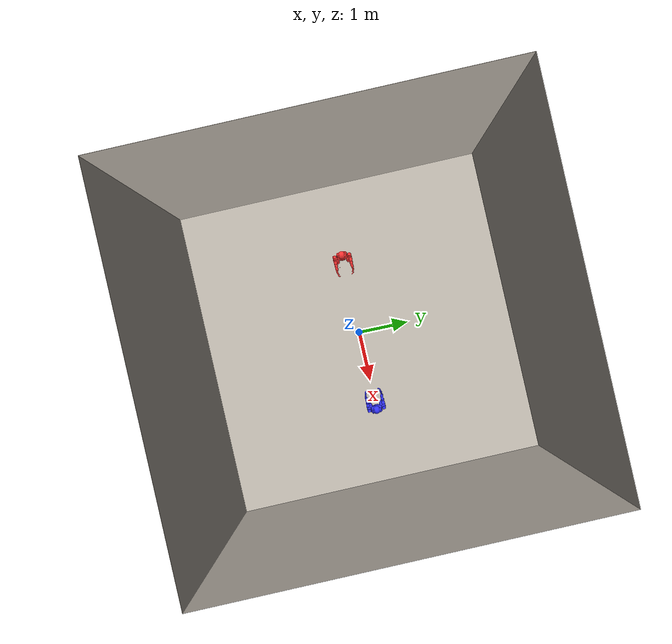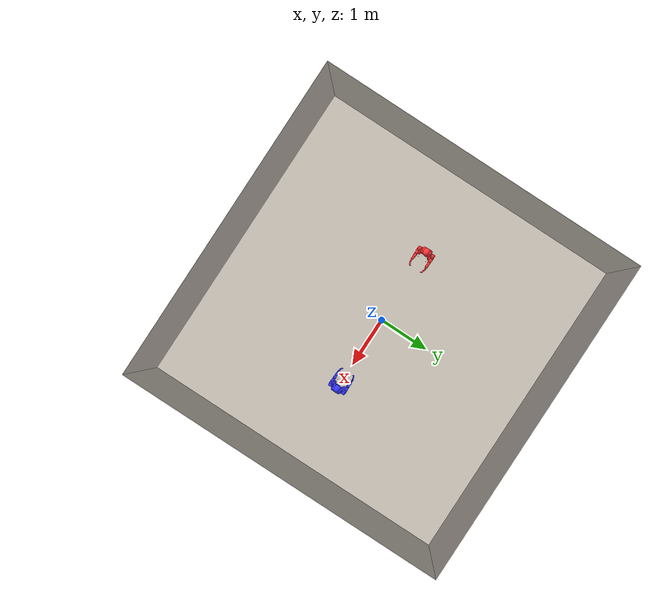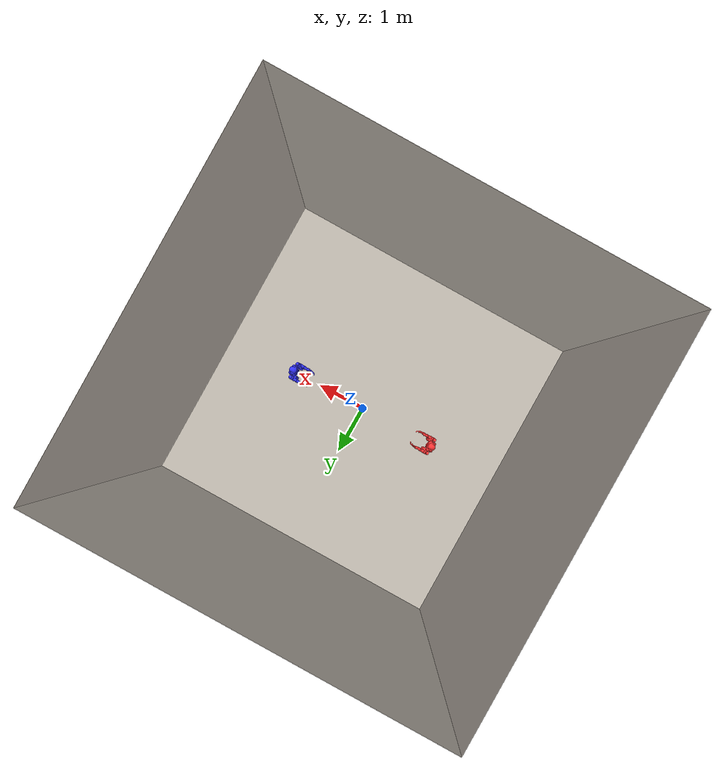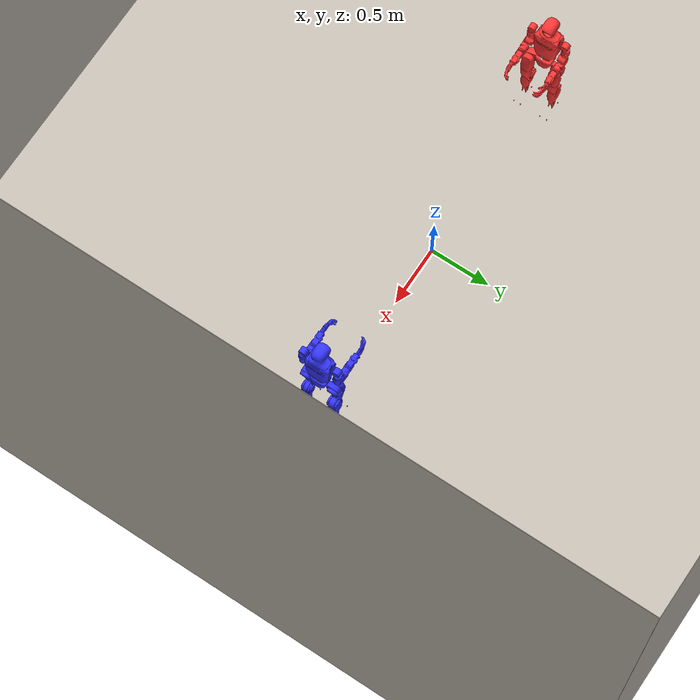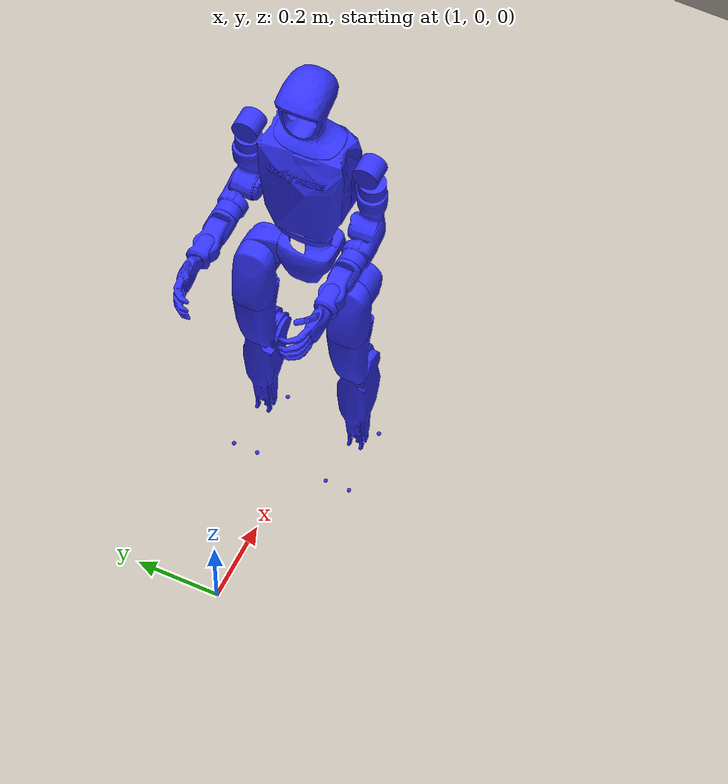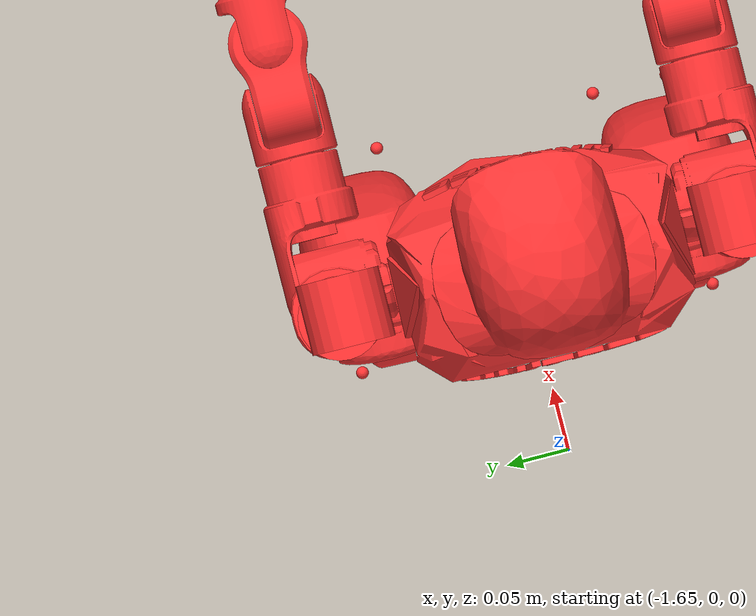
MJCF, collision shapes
<?xml version='1.0' encoding='utf-8'?>
<mujoco model="Laddermoon_Arena">
    <sensor><jointpos name="left_hip_pitch_pos_red" joint="left_hip_pitch_joint_red" />
    <jointpos name="left_hip_roll_pos_red" joint="left_hip_roll_joint_red" />
    <jointpos name="left_hip_yaw_pos_red" joint="left_hip_yaw_joint_red" />
    <jointpos name="left_knee_pos_red" joint="left_knee_joint_red" />
    <jointpos name="left_ankle_pitch_pos_red" joint="left_ankle_pitch_joint_red" />
    <jointpos name="left_ankle_roll_pos_red" joint="left_ankle_roll_joint_red" />
    <jointpos name="right_hip_pitch_pos_red" joint="right_hip_pitch_joint_red" />
    <jointpos name="right_hip_roll_pos_red" joint="right_hip_roll_joint_red" />
    <jointpos name="right_hip_yaw_pos_red" joint="right_hip_yaw_joint_red" />
    <jointpos name="right_knee_pos_red" joint="right_knee_joint_red" />
    <jointpos name="right_ankle_pitch_pos_red" joint="right_ankle_pitch_joint_red" />
    <jointpos name="right_ankle_roll_pos_red" joint="right_ankle_roll_joint_red" />
    <jointpos name="waist_yaw_pos_red" joint="waist_yaw_joint_red" />
    <jointpos name="waist_roll_pos_red" joint="waist_roll_joint_red" />
    <jointpos name="waist_pitch_pos_red" joint="waist_pitch_joint_red" />
    <jointpos name="left_shoulder_pitch_pos_red" joint="left_shoulder_pitch_joint_red" />
    <jointpos name="left_shoulder_roll_pos_red" joint="left_shoulder_roll_joint_red" />
    <jointpos name="left_shoulder_yaw_pos_red" joint="left_shoulder_yaw_joint_red" />
    <jointpos name="left_elbow_pos_red" joint="left_elbow_joint_red" />
    <jointpos name="left_wrist_roll_pos_red" joint="left_wrist_roll_joint_red" />
    <jointpos name="left_wrist_pitch_pos_red" joint="left_wrist_pitch_joint_red" />
    <jointpos name="left_wrist_yaw_pos_red" joint="left_wrist_yaw_joint_red" />
    <jointpos name="right_shoulder_pitch_pos_red" joint="right_shoulder_pitch_joint_red" />
    <jointpos name="right_shoulder_roll_pos_red" joint="right_shoulder_roll_joint_red" />
    <jointpos name="right_shoulder_yaw_pos_red" joint="right_shoulder_yaw_joint_red" />
    <jointpos name="right_elbow_pos_red" joint="right_elbow_joint_red" />
    <jointpos name="right_wrist_roll_pos_red" joint="right_wrist_roll_joint_red" />
    <jointpos name="right_wrist_pitch_pos_red" joint="right_wrist_pitch_joint_red" />
    <jointpos name="right_wrist_yaw_pos_red" joint="right_wrist_yaw_joint_red" />

    <jointvel name="left_hip_pitch_vel_red" joint="left_hip_pitch_joint_red" />
    <jointvel name="left_hip_roll_vel_red" joint="left_hip_roll_joint_red" />
    <jointvel name="left_hip_yaw_vel_red" joint="left_hip_yaw_joint_red" />
    <jointvel name="left_knee_vel_red" joint="left_knee_joint_red" />
    <jointvel name="left_ankle_pitch_vel_red" joint="left_ankle_pitch_joint_red" />
    <jointvel name="left_ankle_roll_vel_red" joint="left_ankle_roll_joint_red" />
    <jointvel name="right_hip_pitch_vel_red" joint="right_hip_pitch_joint_red" />
    <jointvel name="right_hip_roll_vel_red" joint="right_hip_roll_joint_red" />
    <jointvel name="right_hip_yaw_vel_red" joint="right_hip_yaw_joint_red" />
    <jointvel name="right_knee_vel_red" joint="right_knee_joint_red" />
    <jointvel name="right_ankle_pitch_vel_red" joint="right_ankle_pitch_joint_red" />
    <jointvel name="right_ankle_roll_vel_red" joint="right_ankle_roll_joint_red" />
    <jointvel name="waist_yaw_vel_red" joint="waist_yaw_joint_red" />
    <jointvel name="waist_roll_vel_red" joint="waist_roll_joint_red" />
    <jointvel name="waist_pitch_vel_red" joint="waist_pitch_joint_red" />
    <jointvel name="left_shoulder_pitch_vel_red" joint="left_shoulder_pitch_joint_red" />
    <jointvel name="left_shoulder_roll_vel_red" joint="left_shoulder_roll_joint_red" />
    <jointvel name="left_shoulder_yaw_vel_red" joint="left_shoulder_yaw_joint_red" />
    <jointvel name="left_elbow_vel_red" joint="left_elbow_joint_red" />
    <jointvel name="left_wrist_roll_vel_red" joint="left_wrist_roll_joint_red" />
    <jointvel name="left_wrist_pitch_vel_red" joint="left_wrist_pitch_joint_red" />
    <jointvel name="left_wrist_yaw_vel_red" joint="left_wrist_yaw_joint_red" />
    <jointvel name="right_shoulder_pitch_vel_red" joint="right_shoulder_pitch_joint_red" />
    <jointvel name="right_shoulder_roll_vel_red" joint="right_shoulder_roll_joint_red" />
    <jointvel name="right_shoulder_yaw_vel_red" joint="right_shoulder_yaw_joint_red" />
    <jointvel name="right_elbow_vel_red" joint="right_elbow_joint_red" />
    <jointvel name="right_wrist_roll_vel_red" joint="right_wrist_roll_joint_red" />
    <jointvel name="right_wrist_pitch_vel_red" joint="right_wrist_pitch_joint_red" />
    <jointvel name="right_wrist_yaw_vel_red" joint="right_wrist_yaw_joint_red" />

    <jointactuatorfrc name="left_hip_pitch_torque_red" joint="left_hip_pitch_joint_red" />
    <jointactuatorfrc name="left_hip_roll_torque_red" joint="left_hip_roll_joint_red" />
    <jointactuatorfrc name="left_hip_yaw_torque_red" joint="left_hip_yaw_joint_red" />
    <jointactuatorfrc name="left_knee_torque_red" joint="left_knee_joint_red" />
    <jointactuatorfrc name="left_ankle_pitch_torque_red" joint="left_ankle_pitch_joint_red" />
    <jointactuatorfrc name="left_ankle_roll_torque_red" joint="left_ankle_roll_joint_red" />
    <jointactuatorfrc name="right_hip_pitch_torque_red" joint="right_hip_pitch_joint_red" />
    <jointactuatorfrc name="right_hip_roll_torque_red" joint="right_hip_roll_joint_red" />
    <jointactuatorfrc name="right_hip_yaw_torque_red" joint="right_hip_yaw_joint_red" />
    <jointactuatorfrc name="right_knee_torque_red" joint="right_knee_joint_red" />
    <jointactuatorfrc name="right_ankle_pitch_torque_red" joint="right_ankle_pitch_joint_red" />
    <jointactuatorfrc name="right_ankle_roll_torque_red" joint="right_ankle_roll_joint_red" />
    <jointactuatorfrc name="waist_yaw_torque_red" joint="waist_yaw_joint_red" />
    <jointactuatorfrc name="waist_roll_torque_red" joint="waist_roll_joint_red" />
    <jointactuatorfrc name="waist_pitch_torque_red" joint="waist_pitch_joint_red" />
    <jointactuatorfrc name="left_shoulder_pitch_torque_red" joint="left_shoulder_pitch_joint_red" />
    <jointactuatorfrc name="left_shoulder_roll_torque_red" joint="left_shoulder_roll_joint_red" />
    <jointactuatorfrc name="left_shoulder_yaw_torque_red" joint="left_shoulder_yaw_joint_red" />
    <jointactuatorfrc name="left_elbow_torque_red" joint="left_elbow_joint_red" />
    <jointactuatorfrc name="left_wrist_roll_torque_red" joint="left_wrist_roll_joint_red" />
    <jointactuatorfrc name="left_wrist_pitch_torque_red" joint="left_wrist_pitch_joint_red" />
    <jointactuatorfrc name="left_wrist_yaw_torque_red" joint="left_wrist_yaw_joint_red" />
    <jointactuatorfrc name="right_shoulder_pitch_torque_red" joint="right_shoulder_pitch_joint_red" />
    <jointactuatorfrc name="right_shoulder_roll_torque_red" joint="right_shoulder_roll_joint_red" />
    <jointactuatorfrc name="right_shoulder_yaw_torque_red" joint="right_shoulder_yaw_joint_red" />
    <jointactuatorfrc name="right_elbow_torque_red" joint="right_elbow_joint_red" />
    <jointactuatorfrc name="right_wrist_roll_torque_red" joint="right_wrist_roll_joint_red" />
    <jointactuatorfrc name="right_wrist_pitch_torque_red" joint="right_wrist_pitch_joint_red" />
    <jointactuatorfrc name="right_wrist_yaw_torque_red" joint="right_wrist_yaw_joint_red" />

    <framequat name="imu_quat_red" objtype="site" objname="imu_red" />
    <gyro name="imu_gyro_red" site="imu_red" />
    <accelerometer name="imu_acc_red" site="imu_red" />

    <framepos name="frame_pos_red" objtype="site" objname="imu_red" />
    <framelinvel name="frame_vel_red" objtype="site" objname="imu_red" />
  <force site="left_foot_contact_1_red" />
      <force site="left_foot_contact_2_red" />
      <force site="left_foot_contact_3_red" />
      <force site="left_foot_contact_4_red" />
      <force site="right_foot_contact_1_red" />
      <force site="right_foot_contact_2_red" />
      <force site="right_foot_contact_3_red" />
      <force site="right_foot_contact_4_red" />
  <jointpos name="left_hip_pitch_pos_blue" joint="left_hip_pitch_joint_blue" />
    <jointpos name="left_hip_roll_pos_blue" joint="left_hip_roll_joint_blue" />
    <jointpos name="left_hip_yaw_pos_blue" joint="left_hip_yaw_joint_blue" />
    <jointpos name="left_knee_pos_blue" joint="left_knee_joint_blue" />
    <jointpos name="left_ankle_pitch_pos_blue" joint="left_ankle_pitch_joint_blue" />
    <jointpos name="left_ankle_roll_pos_blue" joint="left_ankle_roll_joint_blue" />
    <jointpos name="right_hip_pitch_pos_blue" joint="right_hip_pitch_joint_blue" />
    <jointpos name="right_hip_roll_pos_blue" joint="right_hip_roll_joint_blue" />
    <jointpos name="right_hip_yaw_pos_blue" joint="right_hip_yaw_joint_blue" />
    <jointpos name="right_knee_pos_blue" joint="right_knee_joint_blue" />
    <jointpos name="right_ankle_pitch_pos_blue" joint="right_ankle_pitch_joint_blue" />
    <jointpos name="right_ankle_roll_pos_blue" joint="right_ankle_roll_joint_blue" />
    <jointpos name="waist_yaw_pos_blue" joint="waist_yaw_joint_blue" />
    <jointpos name="waist_roll_pos_blue" joint="waist_roll_joint_blue" />
    <jointpos name="waist_pitch_pos_blue" joint="waist_pitch_joint_blue" />
    <jointpos name="left_shoulder_pitch_pos_blue" joint="left_shoulder_pitch_joint_blue" />
    <jointpos name="left_shoulder_roll_pos_blue" joint="left_shoulder_roll_joint_blue" />
    <jointpos name="left_shoulder_yaw_pos_blue" joint="left_shoulder_yaw_joint_blue" />
    <jointpos name="left_elbow_pos_blue" joint="left_elbow_joint_blue" />
    <jointpos name="left_wrist_roll_pos_blue" joint="left_wrist_roll_joint_blue" />
    <jointpos name="left_wrist_pitch_pos_blue" joint="left_wrist_pitch_joint_blue" />
    <jointpos name="left_wrist_yaw_pos_blue" joint="left_wrist_yaw_joint_blue" />
    <jointpos name="right_shoulder_pitch_pos_blue" joint="right_shoulder_pitch_joint_blue" />
    <jointpos name="right_shoulder_roll_pos_blue" joint="right_shoulder_roll_joint_blue" />
    <jointpos name="right_shoulder_yaw_pos_blue" joint="right_shoulder_yaw_joint_blue" />
    <jointpos name="right_elbow_pos_blue" joint="right_elbow_joint_blue" />
    <jointpos name="right_wrist_roll_pos_blue" joint="right_wrist_roll_joint_blue" />
    <jointpos name="right_wrist_pitch_pos_blue" joint="right_wrist_pitch_joint_blue" />
    <jointpos name="right_wrist_yaw_pos_blue" joint="right_wrist_yaw_joint_blue" />

    <jointvel name="left_hip_pitch_vel_blue" joint="left_hip_pitch_joint_blue" />
    <jointvel name="left_hip_roll_vel_blue" joint="left_hip_roll_joint_blue" />
    <jointvel name="left_hip_yaw_vel_blue" joint="left_hip_yaw_joint_blue" />
    <jointvel name="left_knee_vel_blue" joint="left_knee_joint_blue" />
    <jointvel name="left_ankle_pitch_vel_blue" joint="left_ankle_pitch_joint_blue" />
    <jointvel name="left_ankle_roll_vel_blue" joint="left_ankle_roll_joint_blue" />
    <jointvel name="right_hip_pitch_vel_blue" joint="right_hip_pitch_joint_blue" />
    <jointvel name="right_hip_roll_vel_blue" joint="right_hip_roll_joint_blue" />
    <jointvel name="right_hip_yaw_vel_blue" joint="right_hip_yaw_joint_blue" />
    <jointvel name="right_knee_vel_blue" joint="right_knee_joint_blue" />
    <jointvel name="right_ankle_pitch_vel_blue" joint="right_ankle_pitch_joint_blue" />
    <jointvel name="right_ankle_roll_vel_blue" joint="right_ankle_roll_joint_blue" />
    <jointvel name="waist_yaw_vel_blue" joint="waist_yaw_joint_blue" />
    <jointvel name="waist_roll_vel_blue" joint="waist_roll_joint_blue" />
    <jointvel name="waist_pitch_vel_blue" joint="waist_pitch_joint_blue" />
    <jointvel name="left_shoulder_pitch_vel_blue" joint="left_shoulder_pitch_joint_blue" />
    <jointvel name="left_shoulder_roll_vel_blue" joint="left_shoulder_roll_joint_blue" />
    <jointvel name="left_shoulder_yaw_vel_blue" joint="left_shoulder_yaw_joint_blue" />
    <jointvel name="left_elbow_vel_blue" joint="left_elbow_joint_blue" />
    <jointvel name="left_wrist_roll_vel_blue" joint="left_wrist_roll_joint_blue" />
    <jointvel name="left_wrist_pitch_vel_blue" joint="left_wrist_pitch_joint_blue" />
    <jointvel name="left_wrist_yaw_vel_blue" joint="left_wrist_yaw_joint_blue" />
    <jointvel name="right_shoulder_pitch_vel_blue" joint="right_shoulder_pitch_joint_blue" />
    <jointvel name="right_shoulder_roll_vel_blue" joint="right_shoulder_roll_joint_blue" />
    <jointvel name="right_shoulder_yaw_vel_blue" joint="right_shoulder_yaw_joint_blue" />
    <jointvel name="right_elbow_vel_blue" joint="right_elbow_joint_blue" />
    <jointvel name="right_wrist_roll_vel_blue" joint="right_wrist_roll_joint_blue" />
    <jointvel name="right_wrist_pitch_vel_blue" joint="right_wrist_pitch_joint_blue" />
    <jointvel name="right_wrist_yaw_vel_blue" joint="right_wrist_yaw_joint_blue" />

    <jointactuatorfrc name="left_hip_pitch_torque_blue" joint="left_hip_pitch_joint_blue" />
    <jointactuatorfrc name="left_hip_roll_torque_blue" joint="left_hip_roll_joint_blue" />
    <jointactuatorfrc name="left_hip_yaw_torque_blue" joint="left_hip_yaw_joint_blue" />
    <jointactuatorfrc name="left_knee_torque_blue" joint="left_knee_joint_blue" />
    <jointactuatorfrc name="left_ankle_pitch_torque_blue" joint="left_ankle_pitch_joint_blue" />
    <jointactuatorfrc name="left_ankle_roll_torque_blue" joint="left_ankle_roll_joint_blue" />
    <jointactuatorfrc name="right_hip_pitch_torque_blue" joint="right_hip_pitch_joint_blue" />
    <jointactuatorfrc name="right_hip_roll_torque_blue" joint="right_hip_roll_joint_blue" />
    <jointactuatorfrc name="right_hip_yaw_torque_blue" joint="right_hip_yaw_joint_blue" />
    <jointactuatorfrc name="right_knee_torque_blue" joint="right_knee_joint_blue" />
    <jointactuatorfrc name="right_ankle_pitch_torque_blue" joint="right_ankle_pitch_joint_blue" />
    <jointactuatorfrc name="right_ankle_roll_torque_blue" joint="right_ankle_roll_joint_blue" />
    <jointactuatorfrc name="waist_yaw_torque_blue" joint="waist_yaw_joint_blue" />
    <jointactuatorfrc name="waist_roll_torque_blue" joint="waist_roll_joint_blue" />
    <jointactuatorfrc name="waist_pitch_torque_blue" joint="waist_pitch_joint_blue" />
    <jointactuatorfrc name="left_shoulder_pitch_torque_blue" joint="left_shoulder_pitch_joint_blue" />
    <jointactuatorfrc name="left_shoulder_roll_torque_blue" joint="left_shoulder_roll_joint_blue" />
    <jointactuatorfrc name="left_shoulder_yaw_torque_blue" joint="left_shoulder_yaw_joint_blue" />
    <jointactuatorfrc name="left_elbow_torque_blue" joint="left_elbow_joint_blue" />
    <jointactuatorfrc name="left_wrist_roll_torque_blue" joint="left_wrist_roll_joint_blue" />
    <jointactuatorfrc name="left_wrist_pitch_torque_blue" joint="left_wrist_pitch_joint_blue" />
    <jointactuatorfrc name="left_wrist_yaw_torque_blue" joint="left_wrist_yaw_joint_blue" />
    <jointactuatorfrc name="right_shoulder_pitch_torque_blue" joint="right_shoulder_pitch_joint_blue" />
    <jointactuatorfrc name="right_shoulder_roll_torque_blue" joint="right_shoulder_roll_joint_blue" />
    <jointactuatorfrc name="right_shoulder_yaw_torque_blue" joint="right_shoulder_yaw_joint_blue" />
    <jointactuatorfrc name="right_elbow_torque_blue" joint="right_elbow_joint_blue" />
    <jointactuatorfrc name="right_wrist_roll_torque_blue" joint="right_wrist_roll_joint_blue" />
    <jointactuatorfrc name="right_wrist_pitch_torque_blue" joint="right_wrist_pitch_joint_blue" />
    <jointactuatorfrc name="right_wrist_yaw_torque_blue" joint="right_wrist_yaw_joint_blue" />

    <framequat name="imu_quat_blue" objtype="site" objname="imu_blue" />
    <gyro name="imu_gyro_blue" site="imu_blue" />
    <accelerometer name="imu_acc_blue" site="imu_blue" />

    <framepos name="frame_pos_blue" objtype="site" objname="imu_blue" />
    <framelinvel name="frame_vel_blue" objtype="site" objname="imu_blue" />
  <force site="left_foot_contact_1_blue" />
      <force site="left_foot_contact_2_blue" />
      <force site="left_foot_contact_3_blue" />
      <force site="left_foot_contact_4_blue" />
      <force site="right_foot_contact_1_blue" />
      <force site="right_foot_contact_2_blue" />
      <force site="right_foot_contact_3_blue" />
      <force site="right_foot_contact_4_blue" />
  </sensor><default><default class="torso_motor_red">
      <joint damping="0.05" armature="0.01" frictionloss="0.2" />
    </default>
    <default class="leg_motor_red">
      <joint damping="0.05" armature="0.01" frictionloss="0.2" />
    </default>
    <default class="ankle_motor_red">
      <joint damping="0.05" armature="0.01" frictionloss="0.2" />
    </default>
    <default class="arm_motor_red">
      <joint damping="0.05" armature="0.01" frictionloss="0.2" />
    </default>
    <default class="wrist_motor_red">
      <joint damping="0.05" armature="0.01" frictionloss="0.1" />
    </default>

  <default class="torso_motor_blue">
      <joint damping="0.05" armature="0.01" frictionloss="0.2" />
    </default>
    <default class="leg_motor_blue">
      <joint damping="0.05" armature="0.01" frictionloss="0.2" />
    </default>
    <default class="ankle_motor_blue">
      <joint damping="0.05" armature="0.01" frictionloss="0.2" />
    </default>
    <default class="arm_motor_blue">
      <joint damping="0.05" armature="0.01" frictionloss="0.2" />
    </default>
    <default class="wrist_motor_blue">
      <joint damping="0.05" armature="0.01" frictionloss="0.1" />
    </default>

  </default><contact /><tendon /><actuator><motor name="left_hip_pitch_red" joint="left_hip_pitch_joint_red" ctrlrange="-88 88" />
    <motor name="left_hip_roll_red" joint="left_hip_roll_joint_red" ctrlrange="-88 88" />
    <motor name="left_hip_yaw_red" joint="left_hip_yaw_joint_red" ctrlrange="-88 88" />
    <motor name="left_knee_red" joint="left_knee_joint_red" ctrlrange="-139 139" />
    <motor name="left_ankle_pitch_red" joint="left_ankle_pitch_joint_red" ctrlrange="-50 50" />
    <motor name="left_ankle_roll_red" joint="left_ankle_roll_joint_red" ctrlrange="-50 50" />

    <motor name="right_hip_pitch_red" joint="right_hip_pitch_joint_red" ctrlrange="-88 88" />
    <motor name="right_hip_roll_red" joint="right_hip_roll_joint_red" ctrlrange="-88 88" />
    <motor name="right_hip_yaw_red" joint="right_hip_yaw_joint_red" ctrlrange="-88 88" />
    <motor name="right_knee_red" joint="right_knee_joint_red" ctrlrange="-139 139" />
    <motor name="right_ankle_pitch_red" joint="right_ankle_pitch_joint_red" ctrlrange="-50 50" />
    <motor name="right_ankle_roll_red" joint="right_ankle_roll_joint_red" ctrlrange="-50 50" />

    <motor name="waist_yaw_red" joint="waist_yaw_joint_red" ctrlrange="-88 88" />
    <motor name="waist_roll_red" joint="waist_roll_joint_red" ctrlrange="-50 50" />
    <motor name="waist_pitch_red" joint="waist_pitch_joint_red" ctrlrange="-50 50" />

    <motor name="left_shoulder_pitch_red" joint="left_shoulder_pitch_joint_red" ctrlrange="-25 25" />
    <motor name="left_shoulder_roll_red" joint="left_shoulder_roll_joint_red" ctrlrange="-25 25" />
    <motor name="left_shoulder_yaw_red" joint="left_shoulder_yaw_joint_red" ctrlrange="-25 25" />
    <motor name="left_elbow_red" joint="left_elbow_joint_red" ctrlrange="-25 25" />
    <motor name="left_wrist_roll_red" joint="left_wrist_roll_joint_red" ctrlrange="-25 25" />
    <motor name="left_wrist_pitch_red" joint="left_wrist_pitch_joint_red" ctrlrange="-5 5" />
    <motor name="left_wrist_yaw_red" joint="left_wrist_yaw_joint_red" ctrlrange="-5 5" />

    <motor name="right_shoulder_pitch_red" joint="right_shoulder_pitch_joint_red" ctrlrange="-25 25" />
    <motor name="right_shoulder_roll_red" joint="right_shoulder_roll_joint_red" ctrlrange="-25 25" />
    <motor name="right_shoulder_yaw_red" joint="right_shoulder_yaw_joint_red" ctrlrange="-25 25" />
    <motor name="right_elbow_red" joint="right_elbow_joint_red" ctrlrange="-25 25" />
    <motor name="right_wrist_roll_red" joint="right_wrist_roll_joint_red" ctrlrange="-25 25" />
    <motor name="right_wrist_pitch_red" joint="right_wrist_pitch_joint_red" ctrlrange="-5 5" />
    <motor name="right_wrist_yaw_red" joint="right_wrist_yaw_joint_red" ctrlrange="-5 5" />
  <motor name="left_hip_pitch_blue" joint="left_hip_pitch_joint_blue" ctrlrange="-88 88" />
    <motor name="left_hip_roll_blue" joint="left_hip_roll_joint_blue" ctrlrange="-88 88" />
    <motor name="left_hip_yaw_blue" joint="left_hip_yaw_joint_blue" ctrlrange="-88 88" />
    <motor name="left_knee_blue" joint="left_knee_joint_blue" ctrlrange="-139 139" />
    <motor name="left_ankle_pitch_blue" joint="left_ankle_pitch_joint_blue" ctrlrange="-50 50" />
    <motor name="left_ankle_roll_blue" joint="left_ankle_roll_joint_blue" ctrlrange="-50 50" />

    <motor name="right_hip_pitch_blue" joint="right_hip_pitch_joint_blue" ctrlrange="-88 88" />
    <motor name="right_hip_roll_blue" joint="right_hip_roll_joint_blue" ctrlrange="-88 88" />
    <motor name="right_hip_yaw_blue" joint="right_hip_yaw_joint_blue" ctrlrange="-88 88" />
    <motor name="right_knee_blue" joint="right_knee_joint_blue" ctrlrange="-139 139" />
    <motor name="right_ankle_pitch_blue" joint="right_ankle_pitch_joint_blue" ctrlrange="-50 50" />
    <motor name="right_ankle_roll_blue" joint="right_ankle_roll_joint_blue" ctrlrange="-50 50" />

    <motor name="waist_yaw_blue" joint="waist_yaw_joint_blue" ctrlrange="-88 88" />
    <motor name="waist_roll_blue" joint="waist_roll_joint_blue" ctrlrange="-50 50" />
    <motor name="waist_pitch_blue" joint="waist_pitch_joint_blue" ctrlrange="-50 50" />

    <motor name="left_shoulder_pitch_blue" joint="left_shoulder_pitch_joint_blue" ctrlrange="-25 25" />
    <motor name="left_shoulder_roll_blue" joint="left_shoulder_roll_joint_blue" ctrlrange="-25 25" />
    <motor name="left_shoulder_yaw_blue" joint="left_shoulder_yaw_joint_blue" ctrlrange="-25 25" />
    <motor name="left_elbow_blue" joint="left_elbow_joint_blue" ctrlrange="-25 25" />
    <motor name="left_wrist_roll_blue" joint="left_wrist_roll_joint_blue" ctrlrange="-25 25" />
    <motor name="left_wrist_pitch_blue" joint="left_wrist_pitch_joint_blue" ctrlrange="-5 5" />
    <motor name="left_wrist_yaw_blue" joint="left_wrist_yaw_joint_blue" ctrlrange="-5 5" />

    <motor name="right_shoulder_pitch_blue" joint="right_shoulder_pitch_joint_blue" ctrlrange="-25 25" />
    <motor name="right_shoulder_roll_blue" joint="right_shoulder_roll_joint_blue" ctrlrange="-25 25" />
    <motor name="right_shoulder_yaw_blue" joint="right_shoulder_yaw_joint_blue" ctrlrange="-25 25" />
    <motor name="right_elbow_blue" joint="right_elbow_joint_blue" ctrlrange="-25 25" />
    <motor name="right_wrist_roll_blue" joint="right_wrist_roll_joint_blue" ctrlrange="-25 25" />
    <motor name="right_wrist_pitch_blue" joint="right_wrist_pitch_joint_blue" ctrlrange="-5 5" />
    <motor name="right_wrist_yaw_blue" joint="right_wrist_yaw_joint_blue" ctrlrange="-5 5" />
  </actuator><compiler angle="radian" meshdir="meshes" />

  <visual>
        <global offwidth="640" offheight="480" />
        <headlight ambient="0.4 0.4 0.4" diffuse="0.4 0.4 0.4" />
    </visual>
    <asset>
        <texture name="tex_floor" type="2d" file="textures/floor.png" />
        <material name="mat_floor" texture="tex_floor" texrepeat="1 1" texuniform="false" emission="1" shininess="0" specular="0" />
        <texture name="tex_ceiling" type="2d" file="textures/ceiling.png" />
        <material name="mat_ceiling" texture="tex_ceiling" texrepeat="1 1" texuniform="false" emission="1" shininess="0" specular="0" />
        <texture name="tex_wall" type="2d" file="textures/wall.png" />
        <material name="mat_wall" texture="tex_wall" texrepeat="1 1" texuniform="false" emission="1" shininess="0" specular="0" />
    <mesh name="pelvis_red" file="pelvis.STL" />
    <mesh name="pelvis_contour_link_red" file="pelvis_contour_link.STL" />
    <mesh name="left_hip_pitch_link_red" file="left_hip_pitch_link.STL" />
    <mesh name="left_hip_roll_link_red" file="left_hip_roll_link.STL" />
    <mesh name="left_hip_yaw_link_red" file="left_hip_yaw_link.STL" />
    <mesh name="left_knee_link_red" file="left_knee_link.STL" />
    <mesh name="left_ankle_pitch_link_red" file="left_ankle_pitch_link.STL" />
    <mesh name="left_ankle_roll_link_red" file="left_ankle_roll_link.STL" />
    <mesh name="right_hip_pitch_link_red" file="right_hip_pitch_link.STL" />
    <mesh name="right_hip_roll_link_red" file="right_hip_roll_link.STL" />
    <mesh name="right_hip_yaw_link_red" file="right_hip_yaw_link.STL" />
    <mesh name="right_knee_link_red" file="right_knee_link.STL" />
    <mesh name="right_ankle_pitch_link_red" file="right_ankle_pitch_link.STL" />
    <mesh name="right_ankle_roll_link_red" file="right_ankle_roll_link.STL" />
    <mesh name="waist_yaw_link_red" file="waist_yaw_link.STL" />
    <mesh name="waist_roll_link_red" file="waist_roll_link.STL" />
    <mesh name="torso_link_red" file="torso_link.STL" />
    <mesh name="logo_link_red" file="logo_link.STL" />
    <mesh name="head_link_red" file="head_link.STL" />
    <mesh name="waist_support_link_red" file="waist_support_link.STL" />
    <mesh name="left_shoulder_pitch_link_red" file="left_shoulder_pitch_link.STL" />
    <mesh name="left_shoulder_roll_link_red" file="left_shoulder_roll_link.STL" />
    <mesh name="left_shoulder_yaw_link_red" file="left_shoulder_yaw_link.STL" />
    <mesh name="left_elbow_link_red" file="left_elbow_link.STL" />
    <mesh name="left_wrist_roll_link_red" file="left_wrist_roll_link.STL" />
    <mesh name="left_wrist_pitch_link_red" file="left_wrist_pitch_link.STL" />
    <mesh name="left_wrist_yaw_link_red" file="left_wrist_yaw_link.STL" />
    <mesh name="left_rubber_hand_red" file="left_rubber_hand.STL" />
    <mesh name="right_shoulder_pitch_link_red" file="right_shoulder_pitch_link.STL" />
    <mesh name="right_shoulder_roll_link_red" file="right_shoulder_roll_link.STL" />
    <mesh name="right_shoulder_yaw_link_red" file="right_shoulder_yaw_link.STL" />
    <mesh name="right_elbow_link_red" file="right_elbow_link.STL" />
    <mesh name="right_wrist_roll_link_red" file="right_wrist_roll_link.STL" />
    <mesh name="right_wrist_pitch_link_red" file="right_wrist_pitch_link.STL" />
    <mesh name="right_wrist_yaw_link_red" file="right_wrist_yaw_link.STL" />
    <mesh name="right_rubber_hand_red" file="right_rubber_hand.STL" />
  <mesh name="pelvis_blue" file="pelvis.STL" />
    <mesh name="pelvis_contour_link_blue" file="pelvis_contour_link.STL" />
    <mesh name="left_hip_pitch_link_blue" file="left_hip_pitch_link.STL" />
    <mesh name="left_hip_roll_link_blue" file="left_hip_roll_link.STL" />
    <mesh name="left_hip_yaw_link_blue" file="left_hip_yaw_link.STL" />
    <mesh name="left_knee_link_blue" file="left_knee_link.STL" />
    <mesh name="left_ankle_pitch_link_blue" file="left_ankle_pitch_link.STL" />
    <mesh name="left_ankle_roll_link_blue" file="left_ankle_roll_link.STL" />
    <mesh name="right_hip_pitch_link_blue" file="right_hip_pitch_link.STL" />
    <mesh name="right_hip_roll_link_blue" file="right_hip_roll_link.STL" />
    <mesh name="right_hip_yaw_link_blue" file="right_hip_yaw_link.STL" />
    <mesh name="right_knee_link_blue" file="right_knee_link.STL" />
    <mesh name="right_ankle_pitch_link_blue" file="right_ankle_pitch_link.STL" />
    <mesh name="right_ankle_roll_link_blue" file="right_ankle_roll_link.STL" />
    <mesh name="waist_yaw_link_blue" file="waist_yaw_link.STL" />
    <mesh name="waist_roll_link_blue" file="waist_roll_link.STL" />
    <mesh name="torso_link_blue" file="torso_link.STL" />
    <mesh name="logo_link_blue" file="logo_link.STL" />
    <mesh name="head_link_blue" file="head_link.STL" />
    <mesh name="waist_support_link_blue" file="waist_support_link.STL" />
    <mesh name="left_shoulder_pitch_link_blue" file="left_shoulder_pitch_link.STL" />
    <mesh name="left_shoulder_roll_link_blue" file="left_shoulder_roll_link.STL" />
    <mesh name="left_shoulder_yaw_link_blue" file="left_shoulder_yaw_link.STL" />
    <mesh name="left_elbow_link_blue" file="left_elbow_link.STL" />
    <mesh name="left_wrist_roll_link_blue" file="left_wrist_roll_link.STL" />
    <mesh name="left_wrist_pitch_link_blue" file="left_wrist_pitch_link.STL" />
    <mesh name="left_wrist_yaw_link_blue" file="left_wrist_yaw_link.STL" />
    <mesh name="left_rubber_hand_blue" file="left_rubber_hand.STL" />
    <mesh name="right_shoulder_pitch_link_blue" file="right_shoulder_pitch_link.STL" />
    <mesh name="right_shoulder_roll_link_blue" file="right_shoulder_roll_link.STL" />
    <mesh name="right_shoulder_yaw_link_blue" file="right_shoulder_yaw_link.STL" />
    <mesh name="right_elbow_link_blue" file="right_elbow_link.STL" />
    <mesh name="right_wrist_roll_link_blue" file="right_wrist_roll_link.STL" />
    <mesh name="right_wrist_pitch_link_blue" file="right_wrist_pitch_link.STL" />
    <mesh name="right_wrist_yaw_link_blue" file="right_wrist_yaw_link.STL" />
    <mesh name="right_rubber_hand_blue" file="right_rubber_hand.STL" />
  </asset>
    <worldbody>
        <light name="西南角灯" pos="-3 -3 5" directional="false" />
        <light name="东南角灯" pos="3 -3 5" directional="false" />
        <light name="西北角灯" pos="-3 3 5" directional="false" />
        <light name="东北角灯" pos="3 3 5" directional="false" />
        <camera name="西南角摄像机" pos="-3 -3 4" xyaxes="0.7071 -0.7071 0.0000 0.3590 0.3590 0.8615" />
        <camera name="东南角摄像机" pos="3 -3 4" xyaxes="0.7071 0.7071 -0.0000 -0.3590 0.3590 0.8615" />
        <camera name="西北角摄像机" pos="-3 3 4" xyaxes="-0.7071 -0.7071 0.0000 0.3590 -0.3590 0.8615" />
        <camera name="东北角摄像机" pos="3 3 4" xyaxes="-0.7071 0.7071 0.0000 -0.3590 -0.3590 0.8615" />
        <camera name="南墙摄像机" pos="0 -3 3" xyaxes="1.0000 -0.0000 0.0000 0.0000 0.4472 0.8944" />
        <camera name="北墙摄像机" pos="0 3 3" xyaxes="-1.0000 -0.0000 0.0000 0.0000 -0.4472 0.8944" />
        <camera name="西墙摄像机" pos="-3 0 3" xyaxes="0.0000 -1.0000 0.0000 0.4472 0.0000 0.8944" />
        <camera name="东墙摄像机" pos="3 0 3" xyaxes="0.0000 1.0000 -0.0000 -0.4472 0.0000 0.8944" />
        <camera name="天花板摄像机" pos="0 0 6" xyaxes="1.0000 0.0000 0.0000 -0.0000 1.0000 0.0000" />
        <geom name="地面" type="plane" pos="0.0 0.0 0.0" size="3.05 3.05 0.1" xyaxes="1.0000 0.0000 0.0000 0.0000 1.0000 0.0000" material="mat_floor" />
        <geom name="天花板" type="plane" pos="0.0 0.0 6.1" size="3.05 3.05 0.1" xyaxes="-1.0000 0.0000 0.0000 0.0000 1.0000 0.0000" material="mat_ceiling" />
        <geom name="南墙" type="plane" pos="0.0 -3.05 3.05" size="3.05 3.05 0.1" xyaxes="-1.0000 -0.0000 0.0000 0.0000 0.0000 1.0000" material="mat_wall" />
        <geom name="北墙" type="plane" pos="0.0 3.05 3.05" size="3.05 3.05 0.1" xyaxes="1.0000 0.0000 -0.0000 0.0000 0.0000 1.0000" material="mat_wall" />
        <geom name="西墙" type="plane" pos="-3.05 0.0 3.05" size="3.05 3.05 0.1" xyaxes="0.0000 1.0000 0.0000 0.0000 0.0000 1.0000" material="mat_wall" />
        <geom name="东墙" type="plane" pos="3.05 0.0 3.05" size="3.05 3.05 0.1" xyaxes="-0.0000 -1.0000 -0.0000 0.0000 0.0000 1.0000" material="mat_wall" />
    <body name="pelvis_red" pos="-1.5 0 0.793" euler="0 0 0.0">
      <inertial pos="0 0 -0.07605" quat="1 0 -0.000399148 0" mass="3.813" diaginertia="0.010549 0.0093089 0.0079184" />
      <joint name="floating_base_joint_red" type="free" limited="false" actuatorfrclimited="false" />
      <geom type="mesh" contype="0" conaffinity="0" group="1" density="0" rgba="1 0.2 0.2 1" mesh="pelvis_red" />
      <geom type="mesh" contype="0" conaffinity="0" group="1" density="0" rgba="1 0.2 0.2 1" mesh="pelvis_contour_link_red" />
      <geom type="mesh" rgba="1 0.2 0.2 1" mesh="pelvis_contour_link_red" />
      <body name="left_hip_pitch_link_red" pos="0 0.064452 -0.1027">
        <inertial pos="0.002741 0.047791 -0.02606" quat="0.954862 0.293964 0.0302556 0.030122" mass="1.35" diaginertia="0.00181517 0.00153422 0.00116212" />
        <joint name="left_hip_pitch_joint_red" pos="0 0 0" axis="0 1 0" range="-2.5307 2.8798" actuatorfrcrange="-88 88" class="leg_motor_red" />
        <geom type="mesh" contype="0" conaffinity="0" group="1" density="0" rgba="1 0.2 0.2 1" mesh="left_hip_pitch_link_red" />
        <geom type="mesh" rgba="1 0.2 0.2 1" mesh="left_hip_pitch_link_red" />
        <body name="left_hip_roll_link_red" pos="0 0.052 -0.030465" quat="0.996179 0 -0.0873386 0">
          <inertial pos="0.029812 -0.001045 -0.087934" quat="0.977808 -1.97119e-05 0.205576 -0.0403793" mass="1.52" diaginertia="0.00254986 0.00241169 0.00148755" />
          <joint name="left_hip_roll_joint_red" pos="0 0 0" axis="1 0 0" range="-0.5236 2.9671" actuatorfrcrange="-88 88" class="leg_motor_red" />
          <geom type="mesh" contype="0" conaffinity="0" group="1" density="0" rgba="1 0.2 0.2 1" mesh="left_hip_roll_link_red" />
          <geom type="mesh" rgba="1 0.2 0.2 1" mesh="left_hip_roll_link_red" />
          <body name="left_hip_yaw_link_red" pos="0.025001 0 -0.12412">
            <inertial pos="-0.057709 -0.010981 -0.15078" quat="0.600598 0.15832 0.223482 0.751181" mass="1.702" diaginertia="0.00776166 0.00717575 0.00160139" />
            <joint name="left_hip_yaw_joint_red" pos="0 0 0" axis="0 0 1" range="-2.7576 2.7576" actuatorfrcrange="-88 88" class="leg_motor_red" />
            <geom type="mesh" contype="0" conaffinity="0" group="1" density="0" rgba="1 0.2 0.2 1" mesh="left_hip_yaw_link_red" />
            <geom type="mesh" rgba="1 0.2 0.2 1" mesh="left_hip_yaw_link_red" />
            <body name="left_knee_link_red" pos="-0.078273 0.0021489 -0.17734" quat="0.996179 0 0.0873386 0">
              <inertial pos="0.005457 0.003964 -0.12074" quat="0.923418 -0.0327699 0.0158246 0.382067" mass="1.932" diaginertia="0.0113804 0.0112778 0.00146458" />
              <joint name="left_knee_joint_red" pos="0 0 0" axis="0 1 0" range="-0.087267 2.8798" actuatorfrcrange="-139 139" class="leg_motor_red" />
              <geom type="mesh" contype="0" conaffinity="0" group="1" density="0" rgba="1 0.2 0.2 1" mesh="left_knee_link_red" />
              <geom type="mesh" rgba="1 0.2 0.2 1" mesh="left_knee_link_red" />
              <body name="left_ankle_pitch_link_red" pos="0 -9.4445e-05 -0.30001">
                <inertial pos="-0.007269 0 0.011137" quat="0.603053 0.369225 0.369225 0.603053" mass="0.074" diaginertia="1.89e-05 1.40805e-05 6.9195e-06" />
                <joint name="left_ankle_pitch_joint_red" pos="0 0 0" axis="0 1 0" range="-0.87267 0.5236" actuatorfrcrange="-50 50" class="ankle_motor_red" />
                <geom type="mesh" contype="0" conaffinity="0" group="1" density="0" rgba="1 0.2 0.2 1" mesh="left_ankle_pitch_link_red" />
                <geom type="mesh" rgba="1 0.2 0.2 1" mesh="left_ankle_pitch_link_red" />
                <body name="left_ankle_roll_link_red" pos="0 0 -0.017558">
                  <inertial pos="0.026505 0 -0.016425" quat="-0.000481092 0.728482 -0.000618967 0.685065" mass="0.608" diaginertia="0.00167218 0.0016161 0.000217621" />
                  <joint name="left_ankle_roll_joint_red" pos="0 0 0" axis="1 0 0" range="-0.2618 0.2618" actuatorfrcrange="-50 50" class="ankle_motor_red" />
                  <geom type="mesh" contype="0" conaffinity="0" group="1" density="0" rgba="1 0.2 0.2 1" mesh="left_ankle_roll_link_red" />
                  <body name="dummy_lf_1_red">
                      <inertial pos="0 0 0" mass="0.0001" diaginertia="0 0 0" />
                      <geom size="0.005" pos="-0.05 0.025 -0.03" rgba="1 0.2 0.2 1" />
                      <site name="left_foot_contact_1_red" pos="-0.05 0.025 -0.03" size="0.005" />
                  </body>
                  <body name="dummy_lf_2_red">
                      <inertial pos="0 0 0" mass="0.0001" diaginertia="0 0 0" />
                      <geom size="0.005" pos="-0.05 -0.025 -0.03" rgba="1 0.2 0.2 1" />
                      <site name="left_foot_contact_2_red" pos="-0.05 -0.025 -0.03" size="0.005" />
                  </body>
                  <body name="dummy_lf_3_red">
                      <inertial pos="0 0 0" mass="0.0001" diaginertia="0 0 0" />
                      <geom size="0.005" pos="0.12 0.03 -0.03" rgba="1 0.2 0.2 1" />
                      <site name="left_foot_contact_3_red" pos="0.12 0.03 -0.03" size="0.005" />
                  </body>
                  <body name="dummy_lf_4_red">
                      <inertial pos="0 0 0" mass="0.0001" diaginertia="0 0 0" />
                      <geom size="0.005" pos="0.12 -0.03 -0.03" rgba="1 0.2 0.2 1" />
                      <site name="left_foot_contact_4_red" pos="0.12 -0.03 -0.03" size="0.005" />
                  </body>
                </body>
              </body>
            </body>
          </body>
        </body>
      </body>
      <body name="right_hip_pitch_link_red" pos="0 -0.064452 -0.1027">
        <inertial pos="0.002741 -0.047791 -0.02606" quat="0.954862 -0.293964 0.0302556 -0.030122" mass="1.35" diaginertia="0.00181517 0.00153422 0.00116212" />
        <joint name="right_hip_pitch_joint_red" pos="0 0 0" axis="0 1 0" range="-2.5307 2.8798" actuatorfrcrange="-88 88" class="leg_motor_red" />
        <geom type="mesh" contype="0" conaffinity="0" group="1" density="0" rgba="1 0.2 0.2 1" mesh="right_hip_pitch_link_red" />
        <geom type="mesh" rgba="1 0.2 0.2 1" mesh="right_hip_pitch_link_red" />
        <body name="right_hip_roll_link_red" pos="0 -0.052 -0.030465" quat="0.996179 0 -0.0873386 0">
          <inertial pos="0.029812 0.001045 -0.087934" quat="0.977808 1.97119e-05 0.205576 0.0403793" mass="1.52" diaginertia="0.00254986 0.00241169 0.00148755" />
          <joint name="right_hip_roll_joint_red" pos="0 0 0" axis="1 0 0" range="-2.9671 0.5236" actuatorfrcrange="-88 88" class="leg_motor_red" />
          <geom type="mesh" contype="0" conaffinity="0" group="1" density="0" rgba="1 0.2 0.2 1" mesh="right_hip_roll_link_red" />
          <geom type="mesh" rgba="1 0.2 0.2 1" mesh="right_hip_roll_link_red" />
          <body name="right_hip_yaw_link_red" pos="0.025001 0 -0.12412">
            <inertial pos="-0.057709 0.010981 -0.15078" quat="0.751181 0.223482 0.15832 0.600598" mass="1.702" diaginertia="0.00776166 0.00717575 0.00160139" />
            <joint name="right_hip_yaw_joint_red" pos="0 0 0" axis="0 0 1" range="-2.7576 2.7576" actuatorfrcrange="-88 88" class="leg_motor_red" />
            <geom type="mesh" contype="0" conaffinity="0" group="1" density="0" rgba="1 0.2 0.2 1" mesh="right_hip_yaw_link_red" />
            <geom type="mesh" rgba="1 0.2 0.2 1" mesh="right_hip_yaw_link_red" />
            <body name="right_knee_link_red" pos="-0.078273 -0.0021489 -0.17734" quat="0.996179 0 0.0873386 0">
              <inertial pos="0.005457 -0.003964 -0.12074" quat="0.923439 0.0345276 0.0116333 -0.382012" mass="1.932" diaginertia="0.011374 0.0112843 0.00146452" />
              <joint name="right_knee_joint_red" pos="0 0 0" axis="0 1 0" range="-0.087267 2.8798" actuatorfrcrange="-139 139" class="leg_motor_red" />
              <geom type="mesh" contype="0" conaffinity="0" group="1" density="0" rgba="1 0.2 0.2 1" mesh="right_knee_link_red" />
              <geom type="mesh" rgba="1 0.2 0.2 1" mesh="right_knee_link_red" />
              <body name="right_ankle_pitch_link_red" pos="0 9.4445e-05 -0.30001">
                <inertial pos="-0.007269 0 0.011137" quat="0.603053 0.369225 0.369225 0.603053" mass="0.074" diaginertia="1.89e-05 1.40805e-05 6.9195e-06" />
                <joint name="right_ankle_pitch_joint_red" pos="0 0 0" axis="0 1 0" range="-0.87267 0.5236" actuatorfrcrange="-50 50" class="ankle_motor_red" />
                <geom type="mesh" contype="0" conaffinity="0" group="1" density="0" rgba="1 0.2 0.2 1" mesh="right_ankle_pitch_link_red" />
                <geom type="mesh" rgba="1 0.2 0.2 1" mesh="right_ankle_pitch_link_red" />
                <body name="right_ankle_roll_link_red" pos="0 0 -0.017558">
                  <inertial pos="0.026505 0 -0.016425" quat="0.000481092 0.728482 0.000618967 0.685065" mass="0.608" diaginertia="0.00167218 0.0016161 0.000217621" />
                  <joint name="right_ankle_roll_joint_red" pos="0 0 0" axis="1 0 0" range="-0.2618 0.2618" actuatorfrcrange="-50 50" class="ankle_motor_red" />
                  <geom type="mesh" contype="0" conaffinity="0" group="1" density="0" rgba="1 0.2 0.2 1" mesh="right_ankle_roll_link_red" />
                  <geom size="0.005" pos="-0.05 0.025 -0.03" rgba="1 0.2 0.2 1" />
                  <geom size="0.005" pos="-0.05 -0.025 -0.03" rgba="1 0.2 0.2 1" />
                  <geom size="0.005" pos="0.12 0.03 -0.03" rgba="1 0.2 0.2 1" />
                  <geom size="0.005" pos="0.12 -0.03 -0.03" rgba="1 0.2 0.2 1" />
                  <body name="dummy_rf_1_red">
                      <inertial pos="0 0 0" mass="0.0001" diaginertia="0 0 0" />
                      <site name="right_foot_contact_1_red" pos="-0.05 0.025 -0.03" size="0.005" />
                  </body>
                  <body name="dummy_rf_2_red">
                      <inertial pos="0 0 0" mass="0.0001" diaginertia="0 0 0" />
                      <site name="right_foot_contact_2_red" pos="-0.05 -0.025 -0.03" size="0.005" />
                  </body>
                  <body name="dummy_rf_3_red">
                      <inertial pos="0 0 0" mass="0.0001" diaginertia="0 0 0" />
                      <site name="right_foot_contact_3_red" pos="0.12 0.03 -0.03" size="0.005" />
                  </body>
                  <body name="dummy_rf_4_red">
                      <inertial pos="0 0 0" mass="0.0001" diaginertia="0 0 0" />
                      <site name="right_foot_contact_4_red" pos="0.12 -0.03 -0.03" size="0.005" />
                  </body>
                </body>
              </body>
            </body>
          </body>
        </body>
      </body>
      <body name="waist_yaw_link_red">
        <inertial pos="0.003964 0 0.018769" quat="-0.0178291 0.628464 0.0282471 0.777121" mass="0.244" diaginertia="0.000158561 0.000124229 9.67669e-05" />
        <joint name="waist_yaw_joint_red" pos="0 0 0" axis="0 0 1" range="-2.618 2.618" actuatorfrcrange="-88 88" class="torso_motor_red" />
        <geom type="mesh" contype="0" conaffinity="0" group="1" density="0" rgba="1 0.2 0.2 1" mesh="waist_yaw_link_red" />
        <body name="waist_roll_link_red" pos="-0.0039635 0 0.035">
          <inertial pos="0 -0.000236 0.010111" quat="0.99979 0.020492 0 0" mass="0.047" diaginertia="7.515e-06 6.40206e-06 3.98394e-06" />
          <joint name="waist_roll_joint_red" pos="0 0 0" axis="1 0 0" range="-0.52 0.52" actuatorfrcrange="-50 50" class="torso_motor_red" />
          <geom type="mesh" contype="0" conaffinity="0" group="1" density="0" rgba="1 0.2 0.2 1" mesh="waist_roll_link_red" />
          <body name="torso_link_red" pos="0 0 0.019">
            <camera name="head_camera_red" pos="0.06 0.0 0.45" euler="0 -0.8 -1.57" />
            <inertial pos="0.00331658 0.000261533 0.179856" quat="0.999831 0.000376204 0.0179895 -0.00377704" mass="9.598" diaginertia="0.12407 0.111951 0.0325382" />
            <joint name="waist_pitch_joint_red" pos="0 0 0" axis="0 1 0" range="-0.52 0.52" actuatorfrcrange="-50 50" class="torso_motor_red" />
            <geom type="mesh" contype="0" conaffinity="0" group="1" density="0" rgba="1 0.2 0.2 1" mesh="torso_link_red" />
            <geom type="mesh" rgba="1 0.2 0.2 1" mesh="torso_link_red" />
            <geom pos="0.0039635 0 -0.054" quat="1 0 0 0" type="mesh" contype="0" conaffinity="0" group="1" density="0" rgba="1 0.2 0.2 1" mesh="logo_link_red" />
            <geom pos="0.0039635 0 -0.054" quat="1 0 0 0" type="mesh" rgba="1 0.2 0.2 1" mesh="logo_link_red" />
            <geom pos="0.0039635 0 -0.054" type="mesh" contype="0" conaffinity="0" group="1" density="0" rgba="1 0.2 0.2 1" mesh="head_link_red" />
            <geom pos="0.0039635 0 -0.054" type="mesh" rgba="1 0.2 0.2 1" mesh="head_link_red" />
            <geom pos="0.0039635 0 -0.054" quat="1 0 0 0" type="mesh" contype="0" conaffinity="0" group="1" density="0" rgba="1 0.2 0.2 1" mesh="waist_support_link_red" />
            <geom pos="0.0039635 0 -0.054" quat="1 0 0 0" type="mesh" rgba="1 0.2 0.2 1" mesh="waist_support_link_red" />
            <site name="imu_red" size="0.01" pos="-0.03959 -0.00224 0.13792" />
            <body name="left_shoulder_pitch_link_red" pos="0.0039563 0.10022 0.23778" quat="0.990264 0.139201 1.38722e-05 -9.86868e-05">
              <inertial pos="0 0.035892 -0.011628" quat="0.654152 0.0130458 -0.326267 0.68225" mass="0.718" diaginertia="0.000465864 0.000432842 0.000406394" />
              <joint name="left_shoulder_pitch_joint_red" pos="0 0 0" axis="0 1 0" range="-3.0892 2.6704" actuatorfrcrange="-25 25" class="arm_motor_red" />
              <geom type="mesh" contype="0" conaffinity="0" group="1" density="0" rgba="1 0.2 0.2 1" mesh="left_shoulder_pitch_link_red" />
              <geom size="0.03 0.025" pos="0 0.04 -0.01" quat="0.707107 0 0.707107 0" type="cylinder" rgba="1 0.2 0.2 1" />
              <body name="left_shoulder_roll_link_red" pos="0 0.038 -0.013831" quat="0.990268 -0.139172 0 0">
                <inertial pos="-0.000227 0.00727 -0.063243" quat="0.701256 -0.0196223 -0.00710317 0.712604" mass="0.643" diaginertia="0.000691311 0.000618011 0.000388977" />
                <joint name="left_shoulder_roll_joint_red" pos="0 0 0" axis="1 0 0" range="-1.5882 2.2515" actuatorfrcrange="-25 25" class="arm_motor_red" />
                <geom type="mesh" contype="0" conaffinity="0" group="1" density="0" rgba="1 0.2 0.2 1" mesh="left_shoulder_roll_link_red" />
                <geom size="0.03 0.015" pos="-0.004 0.006 -0.053" type="cylinder" rgba="1 0.2 0.2 1" />
                <body name="left_shoulder_yaw_link_red" pos="0 0.00624 -0.1032">
                  <inertial pos="0.010773 -0.002949 -0.072009" quat="0.716879 -0.0964829 -0.0679942 0.687134" mass="0.734" diaginertia="0.00106187 0.00103217 0.000400661" />
                  <joint name="left_shoulder_yaw_joint_red" pos="0 0 0" axis="0 0 1" range="-2.618 2.618" actuatorfrcrange="-25 25" class="arm_motor_red" />
                  <geom type="mesh" contype="0" conaffinity="0" group="1" density="0" rgba="1 0.2 0.2 1" mesh="left_shoulder_yaw_link_red" />
                  <geom type="mesh" rgba="1 0.2 0.2 1" mesh="left_shoulder_yaw_link_red" />
                  <body name="left_elbow_link_red" pos="0.015783 0 -0.080518">
                    <inertial pos="0.064956 0.004454 -0.010062" quat="0.541765 0.636132 0.388821 0.388129" mass="0.6" diaginertia="0.000443035 0.000421612 0.000259353" />
                    <joint name="left_elbow_joint_red" pos="0 0 0" axis="0 1 0" range="-1.0472 2.0944" actuatorfrcrange="-25 25" class="arm_motor_red" />
                    <geom type="mesh" contype="0" conaffinity="0" group="1" density="0" rgba="1 0.2 0.2 1" mesh="left_elbow_link_red" />
                    <geom type="mesh" rgba="1 0.2 0.2 1" mesh="left_elbow_link_red" />
                    <body name="left_wrist_roll_link_red" pos="0.1 0.00188791 -0.01">
                      <inertial pos="0.0171394 0.000537591 4.8864e-07" quat="0.575338 0.411667 -0.574906 0.411094" mass="0.085445" diaginertia="5.48211e-05 4.96646e-05 3.57798e-05" />
                      <joint name="left_wrist_roll_joint_red" pos="0 0 0" axis="1 0 0" range="-1.97222 1.97222" actuatorfrcrange="-25 25" class="arm_motor_red" />
                      <geom type="mesh" contype="0" conaffinity="0" group="1" density="0" rgba="1 0.2 0.2 1" mesh="left_wrist_roll_link_red" />
                      <geom type="mesh" rgba="1 0.2 0.2 1" mesh="left_wrist_roll_link_red" />
                      <body name="left_wrist_pitch_link_red" pos="0.038 0 0">
                        <inertial pos="0.0229999 -0.00111685 -0.00111658" quat="0.249998 0.661363 0.293036 0.643608" mass="0.48405" diaginertia="0.000430353 0.000429873 0.000164648" />
                        <joint name="left_wrist_pitch_joint_red" pos="0 0 0" axis="0 1 0" range="-1.61443 1.61443" actuatorfrcrange="-5 5" class="wrist_motor_red" />
                        <geom type="mesh" contype="0" conaffinity="0" group="1" density="0" rgba="1 0.2 0.2 1" mesh="left_wrist_pitch_link_red" />
                        <geom type="mesh" rgba="1 0.2 0.2 1" mesh="left_wrist_pitch_link_red" />
                        <body name="left_wrist_yaw_link_red" pos="0.046 0 0">
                          <inertial pos="0.0708244 0.000191745 0.00161742" quat="0.510571 0.526295 0.468078 0.493188" mass="0.254576" diaginertia="0.000646113 0.000559993 0.000147566" />
                          <joint name="left_wrist_yaw_joint_red" pos="0 0 0" axis="0 0 1" range="-1.61443 1.61443" actuatorfrcrange="-5 5" class="wrist_motor_red" />
                          <geom type="mesh" contype="0" conaffinity="0" group="1" density="0" rgba="1 0.2 0.2 1" mesh="left_wrist_yaw_link_red" />
                          <geom type="mesh" rgba="1 0.2 0.2 1" mesh="left_wrist_yaw_link_red" />
                          <body name="left_rubber_hand_red">
                            <inertial pos="0.0001 0.0001 0.0001" mass="0.0001" diaginertia="0 0 0" />
                            <geom pos="0.0415 0.003 0" quat="1 0 0 0" type="mesh" density="0" rgba="1 0.2 0.2 1" mesh="left_rubber_hand_red" />
                          </body>
                        </body>
                      </body>
                    </body>
                  </body>
                </body>
              </body>
            </body>
            <body name="right_shoulder_pitch_link_red" pos="0.0039563 -0.10021 0.23778" quat="0.990264 -0.139201 1.38722e-05 9.86868e-05">
              <inertial pos="0 -0.035892 -0.011628" quat="0.68225 -0.326267 0.0130458 0.654152" mass="0.718" diaginertia="0.000465864 0.000432842 0.000406394" />
              <joint name="right_shoulder_pitch_joint_red" pos="0 0 0" axis="0 1 0" range="-3.0892 2.6704" actuatorfrcrange="-25 25" class="arm_motor_red" />
              <geom type="mesh" contype="0" conaffinity="0" group="1" density="0" rgba="1 0.2 0.2 1" mesh="right_shoulder_pitch_link_red" />
              <geom size="0.03 0.025" pos="0 -0.04 -0.01" quat="0.707107 0 0.707107 0" type="cylinder" rgba="1 0.2 0.2 1" />
              <body name="right_shoulder_roll_link_red" pos="0 -0.038 -0.013831" quat="0.990268 0.139172 0 0">
                <inertial pos="-0.000227 -0.00727 -0.063243" quat="0.712604 -0.00710317 -0.0196223 0.701256" mass="0.643" diaginertia="0.000691311 0.000618011 0.000388977" />
                <joint name="right_shoulder_roll_joint_red" pos="0 0 0" axis="1 0 0" range="-2.2515 1.5882" actuatorfrcrange="-25 25" class="arm_motor_red" />
                <geom type="mesh" contype="0" conaffinity="0" group="1" density="0" rgba="1 0.2 0.2 1" mesh="right_shoulder_roll_link_red" />
                <geom size="0.03 0.015" pos="-0.004 -0.006 -0.053" type="cylinder" rgba="1 0.2 0.2 1" />
                <body name="right_shoulder_yaw_link_red" pos="0 -0.00624 -0.1032">
                  <inertial pos="0.010773 0.002949 -0.072009" quat="0.687134 -0.0679942 -0.0964829 0.716879" mass="0.734" diaginertia="0.00106187 0.00103217 0.000400661" />
                  <joint name="right_shoulder_yaw_joint_red" pos="0 0 0" axis="0 0 1" range="-2.618 2.618" actuatorfrcrange="-25 25" class="arm_motor_red" />
                  <geom type="mesh" contype="0" conaffinity="0" group="1" density="0" rgba="1 0.2 0.2 1" mesh="right_shoulder_yaw_link_red" />
                  <geom type="mesh" rgba="1 0.2 0.2 1" mesh="right_shoulder_yaw_link_red" />
                  <body name="right_elbow_link_red" pos="0.015783 0 -0.080518">
                    <inertial pos="0.064956 -0.004454 -0.010062" quat="0.388129 0.388821 0.636132 0.541765" mass="0.6" diaginertia="0.000443035 0.000421612 0.000259353" />
                    <joint name="right_elbow_joint_red" pos="0 0 0" axis="0 1 0" range="-1.0472 2.0944" actuatorfrcrange="-25 25" class="arm_motor_red" />
                    <geom type="mesh" contype="0" conaffinity="0" group="1" density="0" rgba="1 0.2 0.2 1" mesh="right_elbow_link_red" />
                    <geom type="mesh" rgba="1 0.2 0.2 1" mesh="right_elbow_link_red" />
                    <body name="right_wrist_roll_link_red" pos="0.1 -0.00188791 -0.01">
                      <inertial pos="0.0171394 -0.000537591 4.8864e-07" quat="0.411667 0.575338 -0.411094 0.574906" mass="0.085445" diaginertia="5.48211e-05 4.96646e-05 3.57798e-05" />
                      <joint name="right_wrist_roll_joint_red" pos="0 0 0" axis="1 0 0" range="-1.97222 1.97222" actuatorfrcrange="-25 25" class="arm_motor_red" />
                      <geom type="mesh" contype="0" conaffinity="0" group="1" density="0" rgba="1 0.2 0.2 1" mesh="right_wrist_roll_link_red" />
                      <geom type="mesh" rgba="1 0.2 0.2 1" mesh="right_wrist_roll_link_red" />
                      <body name="right_wrist_pitch_link_red" pos="0.038 0 0">
                        <inertial pos="0.0229999 0.00111685 -0.00111658" quat="0.643608 0.293036 0.661363 0.249998" mass="0.48405" diaginertia="0.000430353 0.000429873 0.000164648" />
                        <joint name="right_wrist_pitch_joint_red" pos="0 0 0" axis="0 1 0" range="-1.61443 1.61443" actuatorfrcrange="-5 5" class="wrist_motor_red" />
                        <geom type="mesh" contype="0" conaffinity="0" group="1" density="0" rgba="1 0.2 0.2 1" mesh="right_wrist_pitch_link_red" />
                        <geom type="mesh" rgba="1 0.2 0.2 1" mesh="right_wrist_pitch_link_red" />
                        <body name="right_wrist_yaw_link_red" pos="0.046 0 0">
                          <inertial pos="0.0708244 -0.000191745 0.00161742" quat="0.493188 0.468078 0.526295 0.510571" mass="0.254576" diaginertia="0.000646113 0.000559993 0.000147566" />
                          <joint name="right_wrist_yaw_joint_red" pos="0 0 0" axis="0 0 1" range="-1.61443 1.61443" actuatorfrcrange="-5 5" class="wrist_motor_red" />
                          <geom type="mesh" contype="0" conaffinity="0" group="1" density="0" rgba="1 0.2 0.2 1" mesh="right_wrist_yaw_link_red" />
                          <geom type="mesh" rgba="1 0.2 0.2 1" mesh="right_wrist_yaw_link_red" />
                          <body name="right_rubber_hand_red">
                            <inertial pos="0.0001 0.0001 0.0001" mass="0.0001" diaginertia="0 0 0" />
                            <geom pos="0.0415 -0.003 0" quat="1 0 0 0" type="mesh" density="0" rgba="1 0.2 0.2 1" mesh="right_rubber_hand_red" />
                          </body>
                        </body>
                      </body>
                    </body>
                  </body>
                </body>
              </body>
            </body>
          </body>
        </body>
      </body>
    </body>
  <body name="pelvis_blue" pos="1.5 0 0.793" euler="0 0 3.141592653589793">
      <inertial pos="0 0 -0.07605" quat="1 0 -0.000399148 0" mass="3.813" diaginertia="0.010549 0.0093089 0.0079184" />
      <joint name="floating_base_joint_blue" type="free" limited="false" actuatorfrclimited="false" />
      <geom type="mesh" contype="0" conaffinity="0" group="1" density="0" rgba="0.2 0.2 1 1" mesh="pelvis_blue" />
      <geom type="mesh" contype="0" conaffinity="0" group="1" density="0" rgba="0.2 0.2 1 1" mesh="pelvis_contour_link_blue" />
      <geom type="mesh" rgba="0.2 0.2 1 1" mesh="pelvis_contour_link_blue" />
      <body name="left_hip_pitch_link_blue" pos="0 0.064452 -0.1027">
        <inertial pos="0.002741 0.047791 -0.02606" quat="0.954862 0.293964 0.0302556 0.030122" mass="1.35" diaginertia="0.00181517 0.00153422 0.00116212" />
        <joint name="left_hip_pitch_joint_blue" pos="0 0 0" axis="0 1 0" range="-2.5307 2.8798" actuatorfrcrange="-88 88" class="leg_motor_blue" />
        <geom type="mesh" contype="0" conaffinity="0" group="1" density="0" rgba="0.2 0.2 1 1" mesh="left_hip_pitch_link_blue" />
        <geom type="mesh" rgba="0.2 0.2 1 1" mesh="left_hip_pitch_link_blue" />
        <body name="left_hip_roll_link_blue" pos="0 0.052 -0.030465" quat="0.996179 0 -0.0873386 0">
          <inertial pos="0.029812 -0.001045 -0.087934" quat="0.977808 -1.97119e-05 0.205576 -0.0403793" mass="1.52" diaginertia="0.00254986 0.00241169 0.00148755" />
          <joint name="left_hip_roll_joint_blue" pos="0 0 0" axis="1 0 0" range="-0.5236 2.9671" actuatorfrcrange="-88 88" class="leg_motor_blue" />
          <geom type="mesh" contype="0" conaffinity="0" group="1" density="0" rgba="0.2 0.2 1 1" mesh="left_hip_roll_link_blue" />
          <geom type="mesh" rgba="0.2 0.2 1 1" mesh="left_hip_roll_link_blue" />
          <body name="left_hip_yaw_link_blue" pos="0.025001 0 -0.12412">
            <inertial pos="-0.057709 -0.010981 -0.15078" quat="0.600598 0.15832 0.223482 0.751181" mass="1.702" diaginertia="0.00776166 0.00717575 0.00160139" />
            <joint name="left_hip_yaw_joint_blue" pos="0 0 0" axis="0 0 1" range="-2.7576 2.7576" actuatorfrcrange="-88 88" class="leg_motor_blue" />
            <geom type="mesh" contype="0" conaffinity="0" group="1" density="0" rgba="0.2 0.2 1 1" mesh="left_hip_yaw_link_blue" />
            <geom type="mesh" rgba="0.2 0.2 1 1" mesh="left_hip_yaw_link_blue" />
            <body name="left_knee_link_blue" pos="-0.078273 0.0021489 -0.17734" quat="0.996179 0 0.0873386 0">
              <inertial pos="0.005457 0.003964 -0.12074" quat="0.923418 -0.0327699 0.0158246 0.382067" mass="1.932" diaginertia="0.0113804 0.0112778 0.00146458" />
              <joint name="left_knee_joint_blue" pos="0 0 0" axis="0 1 0" range="-0.087267 2.8798" actuatorfrcrange="-139 139" class="leg_motor_blue" />
              <geom type="mesh" contype="0" conaffinity="0" group="1" density="0" rgba="0.2 0.2 1 1" mesh="left_knee_link_blue" />
              <geom type="mesh" rgba="0.2 0.2 1 1" mesh="left_knee_link_blue" />
              <body name="left_ankle_pitch_link_blue" pos="0 -9.4445e-05 -0.30001">
                <inertial pos="-0.007269 0 0.011137" quat="0.603053 0.369225 0.369225 0.603053" mass="0.074" diaginertia="1.89e-05 1.40805e-05 6.9195e-06" />
                <joint name="left_ankle_pitch_joint_blue" pos="0 0 0" axis="0 1 0" range="-0.87267 0.5236" actuatorfrcrange="-50 50" class="ankle_motor_blue" />
                <geom type="mesh" contype="0" conaffinity="0" group="1" density="0" rgba="0.2 0.2 1 1" mesh="left_ankle_pitch_link_blue" />
                <geom type="mesh" rgba="0.2 0.2 1 1" mesh="left_ankle_pitch_link_blue" />
                <body name="left_ankle_roll_link_blue" pos="0 0 -0.017558">
                  <inertial pos="0.026505 0 -0.016425" quat="-0.000481092 0.728482 -0.000618967 0.685065" mass="0.608" diaginertia="0.00167218 0.0016161 0.000217621" />
                  <joint name="left_ankle_roll_joint_blue" pos="0 0 0" axis="1 0 0" range="-0.2618 0.2618" actuatorfrcrange="-50 50" class="ankle_motor_blue" />
                  <geom type="mesh" contype="0" conaffinity="0" group="1" density="0" rgba="0.2 0.2 1 1" mesh="left_ankle_roll_link_blue" />
                  <body name="dummy_lf_1_blue">
                      <inertial pos="0 0 0" mass="0.0001" diaginertia="0 0 0" />
                      <geom size="0.005" pos="-0.05 0.025 -0.03" rgba="0.2 0.2 1 1" />
                      <site name="left_foot_contact_1_blue" pos="-0.05 0.025 -0.03" size="0.005" />
                  </body>
                  <body name="dummy_lf_2_blue">
                      <inertial pos="0 0 0" mass="0.0001" diaginertia="0 0 0" />
                      <geom size="0.005" pos="-0.05 -0.025 -0.03" rgba="0.2 0.2 1 1" />
                      <site name="left_foot_contact_2_blue" pos="-0.05 -0.025 -0.03" size="0.005" />
                  </body>
                  <body name="dummy_lf_3_blue">
                      <inertial pos="0 0 0" mass="0.0001" diaginertia="0 0 0" />
                      <geom size="0.005" pos="0.12 0.03 -0.03" rgba="0.2 0.2 1 1" />
                      <site name="left_foot_contact_3_blue" pos="0.12 0.03 -0.03" size="0.005" />
                  </body>
                  <body name="dummy_lf_4_blue">
                      <inertial pos="0 0 0" mass="0.0001" diaginertia="0 0 0" />
                      <geom size="0.005" pos="0.12 -0.03 -0.03" rgba="0.2 0.2 1 1" />
                      <site name="left_foot_contact_4_blue" pos="0.12 -0.03 -0.03" size="0.005" />
                  </body>
                </body>
              </body>
            </body>
          </body>
        </body>
      </body>
      <body name="right_hip_pitch_link_blue" pos="0 -0.064452 -0.1027">
        <inertial pos="0.002741 -0.047791 -0.02606" quat="0.954862 -0.293964 0.0302556 -0.030122" mass="1.35" diaginertia="0.00181517 0.00153422 0.00116212" />
        <joint name="right_hip_pitch_joint_blue" pos="0 0 0" axis="0 1 0" range="-2.5307 2.8798" actuatorfrcrange="-88 88" class="leg_motor_blue" />
        <geom type="mesh" contype="0" conaffinity="0" group="1" density="0" rgba="0.2 0.2 1 1" mesh="right_hip_pitch_link_blue" />
        <geom type="mesh" rgba="0.2 0.2 1 1" mesh="right_hip_pitch_link_blue" />
        <body name="right_hip_roll_link_blue" pos="0 -0.052 -0.030465" quat="0.996179 0 -0.0873386 0">
          <inertial pos="0.029812 0.001045 -0.087934" quat="0.977808 1.97119e-05 0.205576 0.0403793" mass="1.52" diaginertia="0.00254986 0.00241169 0.00148755" />
          <joint name="right_hip_roll_joint_blue" pos="0 0 0" axis="1 0 0" range="-2.9671 0.5236" actuatorfrcrange="-88 88" class="leg_motor_blue" />
          <geom type="mesh" contype="0" conaffinity="0" group="1" density="0" rgba="0.2 0.2 1 1" mesh="right_hip_roll_link_blue" />
          <geom type="mesh" rgba="0.2 0.2 1 1" mesh="right_hip_roll_link_blue" />
          <body name="right_hip_yaw_link_blue" pos="0.025001 0 -0.12412">
            <inertial pos="-0.057709 0.010981 -0.15078" quat="0.751181 0.223482 0.15832 0.600598" mass="1.702" diaginertia="0.00776166 0.00717575 0.00160139" />
            <joint name="right_hip_yaw_joint_blue" pos="0 0 0" axis="0 0 1" range="-2.7576 2.7576" actuatorfrcrange="-88 88" class="leg_motor_blue" />
            <geom type="mesh" contype="0" conaffinity="0" group="1" density="0" rgba="0.2 0.2 1 1" mesh="right_hip_yaw_link_blue" />
            <geom type="mesh" rgba="0.2 0.2 1 1" mesh="right_hip_yaw_link_blue" />
            <body name="right_knee_link_blue" pos="-0.078273 -0.0021489 -0.17734" quat="0.996179 0 0.0873386 0">
              <inertial pos="0.005457 -0.003964 -0.12074" quat="0.923439 0.0345276 0.0116333 -0.382012" mass="1.932" diaginertia="0.011374 0.0112843 0.00146452" />
              <joint name="right_knee_joint_blue" pos="0 0 0" axis="0 1 0" range="-0.087267 2.8798" actuatorfrcrange="-139 139" class="leg_motor_blue" />
              <geom type="mesh" contype="0" conaffinity="0" group="1" density="0" rgba="0.2 0.2 1 1" mesh="right_knee_link_blue" />
              <geom type="mesh" rgba="0.2 0.2 1 1" mesh="right_knee_link_blue" />
              <body name="right_ankle_pitch_link_blue" pos="0 9.4445e-05 -0.30001">
                <inertial pos="-0.007269 0 0.011137" quat="0.603053 0.369225 0.369225 0.603053" mass="0.074" diaginertia="1.89e-05 1.40805e-05 6.9195e-06" />
                <joint name="right_ankle_pitch_joint_blue" pos="0 0 0" axis="0 1 0" range="-0.87267 0.5236" actuatorfrcrange="-50 50" class="ankle_motor_blue" />
                <geom type="mesh" contype="0" conaffinity="0" group="1" density="0" rgba="0.2 0.2 1 1" mesh="right_ankle_pitch_link_blue" />
                <geom type="mesh" rgba="0.2 0.2 1 1" mesh="right_ankle_pitch_link_blue" />
                <body name="right_ankle_roll_link_blue" pos="0 0 -0.017558">
                  <inertial pos="0.026505 0 -0.016425" quat="0.000481092 0.728482 0.000618967 0.685065" mass="0.608" diaginertia="0.00167218 0.0016161 0.000217621" />
                  <joint name="right_ankle_roll_joint_blue" pos="0 0 0" axis="1 0 0" range="-0.2618 0.2618" actuatorfrcrange="-50 50" class="ankle_motor_blue" />
                  <geom type="mesh" contype="0" conaffinity="0" group="1" density="0" rgba="0.2 0.2 1 1" mesh="right_ankle_roll_link_blue" />
                  <geom size="0.005" pos="-0.05 0.025 -0.03" rgba="0.2 0.2 1 1" />
                  <geom size="0.005" pos="-0.05 -0.025 -0.03" rgba="0.2 0.2 1 1" />
                  <geom size="0.005" pos="0.12 0.03 -0.03" rgba="0.2 0.2 1 1" />
                  <geom size="0.005" pos="0.12 -0.03 -0.03" rgba="0.2 0.2 1 1" />
                  <body name="dummy_rf_1_blue">
                      <inertial pos="0 0 0" mass="0.0001" diaginertia="0 0 0" />
                      <site name="right_foot_contact_1_blue" pos="-0.05 0.025 -0.03" size="0.005" />
                  </body>
                  <body name="dummy_rf_2_blue">
                      <inertial pos="0 0 0" mass="0.0001" diaginertia="0 0 0" />
                      <site name="right_foot_contact_2_blue" pos="-0.05 -0.025 -0.03" size="0.005" />
                  </body>
                  <body name="dummy_rf_3_blue">
                      <inertial pos="0 0 0" mass="0.0001" diaginertia="0 0 0" />
                      <site name="right_foot_contact_3_blue" pos="0.12 0.03 -0.03" size="0.005" />
                  </body>
                  <body name="dummy_rf_4_blue">
                      <inertial pos="0 0 0" mass="0.0001" diaginertia="0 0 0" />
                      <site name="right_foot_contact_4_blue" pos="0.12 -0.03 -0.03" size="0.005" />
                  </body>
                </body>
              </body>
            </body>
          </body>
        </body>
      </body>
      <body name="waist_yaw_link_blue">
        <inertial pos="0.003964 0 0.018769" quat="-0.0178291 0.628464 0.0282471 0.777121" mass="0.244" diaginertia="0.000158561 0.000124229 9.67669e-05" />
        <joint name="waist_yaw_joint_blue" pos="0 0 0" axis="0 0 1" range="-2.618 2.618" actuatorfrcrange="-88 88" class="torso_motor_blue" />
        <geom type="mesh" contype="0" conaffinity="0" group="1" density="0" rgba="0.2 0.2 1 1" mesh="waist_yaw_link_blue" />
        <body name="waist_roll_link_blue" pos="-0.0039635 0 0.035">
          <inertial pos="0 -0.000236 0.010111" quat="0.99979 0.020492 0 0" mass="0.047" diaginertia="7.515e-06 6.40206e-06 3.98394e-06" />
          <joint name="waist_roll_joint_blue" pos="0 0 0" axis="1 0 0" range="-0.52 0.52" actuatorfrcrange="-50 50" class="torso_motor_blue" />
          <geom type="mesh" contype="0" conaffinity="0" group="1" density="0" rgba="0.2 0.2 1 1" mesh="waist_roll_link_blue" />
          <body name="torso_link_blue" pos="0 0 0.019">
            <camera name="head_camera_blue" pos="0.06 0.0 0.45" euler="0 -0.8 -1.57" />
            <inertial pos="0.00331658 0.000261533 0.179856" quat="0.999831 0.000376204 0.0179895 -0.00377704" mass="9.598" diaginertia="0.12407 0.111951 0.0325382" />
            <joint name="waist_pitch_joint_blue" pos="0 0 0" axis="0 1 0" range="-0.52 0.52" actuatorfrcrange="-50 50" class="torso_motor_blue" />
            <geom type="mesh" contype="0" conaffinity="0" group="1" density="0" rgba="0.2 0.2 1 1" mesh="torso_link_blue" />
            <geom type="mesh" rgba="0.2 0.2 1 1" mesh="torso_link_blue" />
            <geom pos="0.0039635 0 -0.054" quat="1 0 0 0" type="mesh" contype="0" conaffinity="0" group="1" density="0" rgba="0.2 0.2 1 1" mesh="logo_link_blue" />
            <geom pos="0.0039635 0 -0.054" quat="1 0 0 0" type="mesh" rgba="0.2 0.2 1 1" mesh="logo_link_blue" />
            <geom pos="0.0039635 0 -0.054" type="mesh" contype="0" conaffinity="0" group="1" density="0" rgba="0.2 0.2 1 1" mesh="head_link_blue" />
            <geom pos="0.0039635 0 -0.054" type="mesh" rgba="0.2 0.2 1 1" mesh="head_link_blue" />
            <geom pos="0.0039635 0 -0.054" quat="1 0 0 0" type="mesh" contype="0" conaffinity="0" group="1" density="0" rgba="0.2 0.2 1 1" mesh="waist_support_link_blue" />
            <geom pos="0.0039635 0 -0.054" quat="1 0 0 0" type="mesh" rgba="0.2 0.2 1 1" mesh="waist_support_link_blue" />
            <site name="imu_blue" size="0.01" pos="-0.03959 -0.00224 0.13792" />
            <body name="left_shoulder_pitch_link_blue" pos="0.0039563 0.10022 0.23778" quat="0.990264 0.139201 1.38722e-05 -9.86868e-05">
              <inertial pos="0 0.035892 -0.011628" quat="0.654152 0.0130458 -0.326267 0.68225" mass="0.718" diaginertia="0.000465864 0.000432842 0.000406394" />
              <joint name="left_shoulder_pitch_joint_blue" pos="0 0 0" axis="0 1 0" range="-3.0892 2.6704" actuatorfrcrange="-25 25" class="arm_motor_blue" />
              <geom type="mesh" contype="0" conaffinity="0" group="1" density="0" rgba="0.2 0.2 1 1" mesh="left_shoulder_pitch_link_blue" />
              <geom size="0.03 0.025" pos="0 0.04 -0.01" quat="0.707107 0 0.707107 0" type="cylinder" rgba="0.2 0.2 1 1" />
              <body name="left_shoulder_roll_link_blue" pos="0 0.038 -0.013831" quat="0.990268 -0.139172 0 0">
                <inertial pos="-0.000227 0.00727 -0.063243" quat="0.701256 -0.0196223 -0.00710317 0.712604" mass="0.643" diaginertia="0.000691311 0.000618011 0.000388977" />
                <joint name="left_shoulder_roll_joint_blue" pos="0 0 0" axis="1 0 0" range="-1.5882 2.2515" actuatorfrcrange="-25 25" class="arm_motor_blue" />
                <geom type="mesh" contype="0" conaffinity="0" group="1" density="0" rgba="0.2 0.2 1 1" mesh="left_shoulder_roll_link_blue" />
                <geom size="0.03 0.015" pos="-0.004 0.006 -0.053" type="cylinder" rgba="0.2 0.2 1 1" />
                <body name="left_shoulder_yaw_link_blue" pos="0 0.00624 -0.1032">
                  <inertial pos="0.010773 -0.002949 -0.072009" quat="0.716879 -0.0964829 -0.0679942 0.687134" mass="0.734" diaginertia="0.00106187 0.00103217 0.000400661" />
                  <joint name="left_shoulder_yaw_joint_blue" pos="0 0 0" axis="0 0 1" range="-2.618 2.618" actuatorfrcrange="-25 25" class="arm_motor_blue" />
                  <geom type="mesh" contype="0" conaffinity="0" group="1" density="0" rgba="0.2 0.2 1 1" mesh="left_shoulder_yaw_link_blue" />
                  <geom type="mesh" rgba="0.2 0.2 1 1" mesh="left_shoulder_yaw_link_blue" />
                  <body name="left_elbow_link_blue" pos="0.015783 0 -0.080518">
                    <inertial pos="0.064956 0.004454 -0.010062" quat="0.541765 0.636132 0.388821 0.388129" mass="0.6" diaginertia="0.000443035 0.000421612 0.000259353" />
                    <joint name="left_elbow_joint_blue" pos="0 0 0" axis="0 1 0" range="-1.0472 2.0944" actuatorfrcrange="-25 25" class="arm_motor_blue" />
                    <geom type="mesh" contype="0" conaffinity="0" group="1" density="0" rgba="0.2 0.2 1 1" mesh="left_elbow_link_blue" />
                    <geom type="mesh" rgba="0.2 0.2 1 1" mesh="left_elbow_link_blue" />
                    <body name="left_wrist_roll_link_blue" pos="0.1 0.00188791 -0.01">
                      <inertial pos="0.0171394 0.000537591 4.8864e-07" quat="0.575338 0.411667 -0.574906 0.411094" mass="0.085445" diaginertia="5.48211e-05 4.96646e-05 3.57798e-05" />
                      <joint name="left_wrist_roll_joint_blue" pos="0 0 0" axis="1 0 0" range="-1.97222 1.97222" actuatorfrcrange="-25 25" class="arm_motor_blue" />
                      <geom type="mesh" contype="0" conaffinity="0" group="1" density="0" rgba="0.2 0.2 1 1" mesh="left_wrist_roll_link_blue" />
                      <geom type="mesh" rgba="0.2 0.2 1 1" mesh="left_wrist_roll_link_blue" />
                      <body name="left_wrist_pitch_link_blue" pos="0.038 0 0">
                        <inertial pos="0.0229999 -0.00111685 -0.00111658" quat="0.249998 0.661363 0.293036 0.643608" mass="0.48405" diaginertia="0.000430353 0.000429873 0.000164648" />
                        <joint name="left_wrist_pitch_joint_blue" pos="0 0 0" axis="0 1 0" range="-1.61443 1.61443" actuatorfrcrange="-5 5" class="wrist_motor_blue" />
                        <geom type="mesh" contype="0" conaffinity="0" group="1" density="0" rgba="0.2 0.2 1 1" mesh="left_wrist_pitch_link_blue" />
                        <geom type="mesh" rgba="0.2 0.2 1 1" mesh="left_wrist_pitch_link_blue" />
                        <body name="left_wrist_yaw_link_blue" pos="0.046 0 0">
                          <inertial pos="0.0708244 0.000191745 0.00161742" quat="0.510571 0.526295 0.468078 0.493188" mass="0.254576" diaginertia="0.000646113 0.000559993 0.000147566" />
                          <joint name="left_wrist_yaw_joint_blue" pos="0 0 0" axis="0 0 1" range="-1.61443 1.61443" actuatorfrcrange="-5 5" class="wrist_motor_blue" />
                          <geom type="mesh" contype="0" conaffinity="0" group="1" density="0" rgba="0.2 0.2 1 1" mesh="left_wrist_yaw_link_blue" />
                          <geom type="mesh" rgba="0.2 0.2 1 1" mesh="left_wrist_yaw_link_blue" />
                          <body name="left_rubber_hand_blue">
                            <inertial pos="0.0001 0.0001 0.0001" mass="0.0001" diaginertia="0 0 0" />
                            <geom pos="0.0415 0.003 0" quat="1 0 0 0" type="mesh" density="0" rgba="0.2 0.2 1 1" mesh="left_rubber_hand_blue" />
                          </body>
                        </body>
                      </body>
                    </body>
                  </body>
                </body>
              </body>
            </body>
            <body name="right_shoulder_pitch_link_blue" pos="0.0039563 -0.10021 0.23778" quat="0.990264 -0.139201 1.38722e-05 9.86868e-05">
              <inertial pos="0 -0.035892 -0.011628" quat="0.68225 -0.326267 0.0130458 0.654152" mass="0.718" diaginertia="0.000465864 0.000432842 0.000406394" />
              <joint name="right_shoulder_pitch_joint_blue" pos="0 0 0" axis="0 1 0" range="-3.0892 2.6704" actuatorfrcrange="-25 25" class="arm_motor_blue" />
              <geom type="mesh" contype="0" conaffinity="0" group="1" density="0" rgba="0.2 0.2 1 1" mesh="right_shoulder_pitch_link_blue" />
              <geom size="0.03 0.025" pos="0 -0.04 -0.01" quat="0.707107 0 0.707107 0" type="cylinder" rgba="0.2 0.2 1 1" />
              <body name="right_shoulder_roll_link_blue" pos="0 -0.038 -0.013831" quat="0.990268 0.139172 0 0">
                <inertial pos="-0.000227 -0.00727 -0.063243" quat="0.712604 -0.00710317 -0.0196223 0.701256" mass="0.643" diaginertia="0.000691311 0.000618011 0.000388977" />
                <joint name="right_shoulder_roll_joint_blue" pos="0 0 0" axis="1 0 0" range="-2.2515 1.5882" actuatorfrcrange="-25 25" class="arm_motor_blue" />
                <geom type="mesh" contype="0" conaffinity="0" group="1" density="0" rgba="0.2 0.2 1 1" mesh="right_shoulder_roll_link_blue" />
                <geom size="0.03 0.015" pos="-0.004 -0.006 -0.053" type="cylinder" rgba="0.2 0.2 1 1" />
                <body name="right_shoulder_yaw_link_blue" pos="0 -0.00624 -0.1032">
                  <inertial pos="0.010773 0.002949 -0.072009" quat="0.687134 -0.0679942 -0.0964829 0.716879" mass="0.734" diaginertia="0.00106187 0.00103217 0.000400661" />
                  <joint name="right_shoulder_yaw_joint_blue" pos="0 0 0" axis="0 0 1" range="-2.618 2.618" actuatorfrcrange="-25 25" class="arm_motor_blue" />
                  <geom type="mesh" contype="0" conaffinity="0" group="1" density="0" rgba="0.2 0.2 1 1" mesh="right_shoulder_yaw_link_blue" />
                  <geom type="mesh" rgba="0.2 0.2 1 1" mesh="right_shoulder_yaw_link_blue" />
                  <body name="right_elbow_link_blue" pos="0.015783 0 -0.080518">
                    <inertial pos="0.064956 -0.004454 -0.010062" quat="0.388129 0.388821 0.636132 0.541765" mass="0.6" diaginertia="0.000443035 0.000421612 0.000259353" />
                    <joint name="right_elbow_joint_blue" pos="0 0 0" axis="0 1 0" range="-1.0472 2.0944" actuatorfrcrange="-25 25" class="arm_motor_blue" />
                    <geom type="mesh" contype="0" conaffinity="0" group="1" density="0" rgba="0.2 0.2 1 1" mesh="right_elbow_link_blue" />
                    <geom type="mesh" rgba="0.2 0.2 1 1" mesh="right_elbow_link_blue" />
                    <body name="right_wrist_roll_link_blue" pos="0.1 -0.00188791 -0.01">
                      <inertial pos="0.0171394 -0.000537591 4.8864e-07" quat="0.411667 0.575338 -0.411094 0.574906" mass="0.085445" diaginertia="5.48211e-05 4.96646e-05 3.57798e-05" />
                      <joint name="right_wrist_roll_joint_blue" pos="0 0 0" axis="1 0 0" range="-1.97222 1.97222" actuatorfrcrange="-25 25" class="arm_motor_blue" />
                      <geom type="mesh" contype="0" conaffinity="0" group="1" density="0" rgba="0.2 0.2 1 1" mesh="right_wrist_roll_link_blue" />
                      <geom type="mesh" rgba="0.2 0.2 1 1" mesh="right_wrist_roll_link_blue" />
                      <body name="right_wrist_pitch_link_blue" pos="0.038 0 0">
                        <inertial pos="0.0229999 0.00111685 -0.00111658" quat="0.643608 0.293036 0.661363 0.249998" mass="0.48405" diaginertia="0.000430353 0.000429873 0.000164648" />
                        <joint name="right_wrist_pitch_joint_blue" pos="0 0 0" axis="0 1 0" range="-1.61443 1.61443" actuatorfrcrange="-5 5" class="wrist_motor_blue" />
                        <geom type="mesh" contype="0" conaffinity="0" group="1" density="0" rgba="0.2 0.2 1 1" mesh="right_wrist_pitch_link_blue" />
                        <geom type="mesh" rgba="0.2 0.2 1 1" mesh="right_wrist_pitch_link_blue" />
                        <body name="right_wrist_yaw_link_blue" pos="0.046 0 0">
                          <inertial pos="0.0708244 -0.000191745 0.00161742" quat="0.493188 0.468078 0.526295 0.510571" mass="0.254576" diaginertia="0.000646113 0.000559993 0.000147566" />
                          <joint name="right_wrist_yaw_joint_blue" pos="0 0 0" axis="0 0 1" range="-1.61443 1.61443" actuatorfrcrange="-5 5" class="wrist_motor_blue" />
                          <geom type="mesh" contype="0" conaffinity="0" group="1" density="0" rgba="0.2 0.2 1 1" mesh="right_wrist_yaw_link_blue" />
                          <geom type="mesh" rgba="0.2 0.2 1 1" mesh="right_wrist_yaw_link_blue" />
                          <body name="right_rubber_hand_blue">
                            <inertial pos="0.0001 0.0001 0.0001" mass="0.0001" diaginertia="0 0 0" />
                            <geom pos="0.0415 -0.003 0" quat="1 0 0 0" type="mesh" density="0" rgba="0.2 0.2 1 1" mesh="right_rubber_hand_blue" />
                          </body>
                        </body>
                      </body>
                    </body>
                  </body>
                </body>
              </body>
            </body>
          </body>
        </body>
      </body>
    </body>
  </worldbody>
</mujoco>
